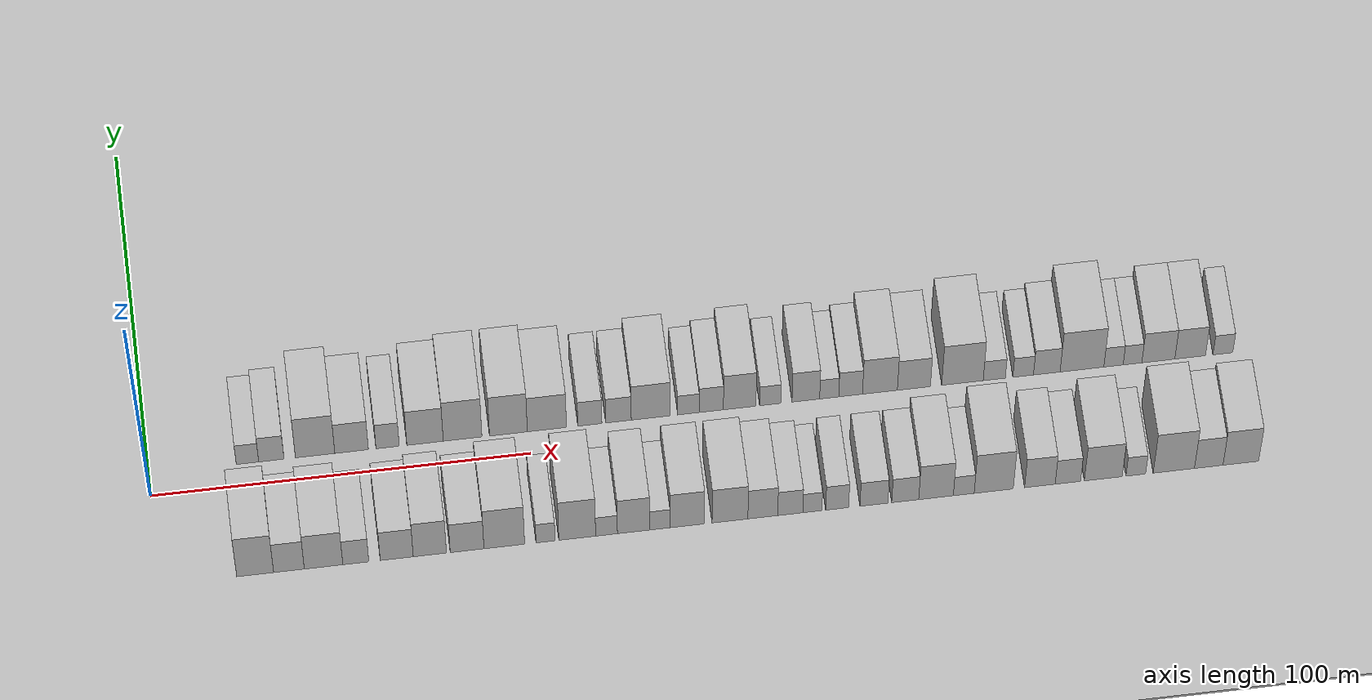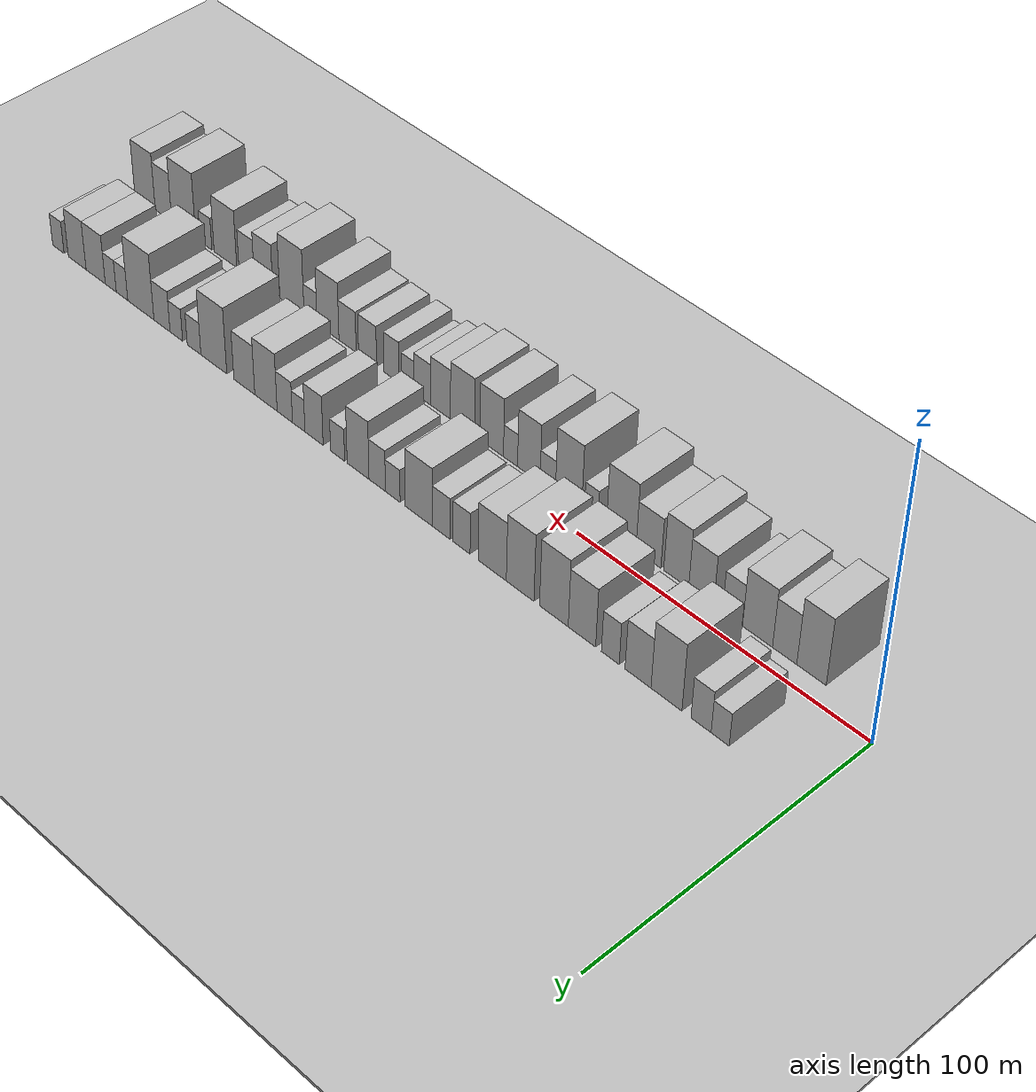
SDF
<?xml version="1.0" encoding="utf-8"?>

<sdf version="1.6">

   <world name="default">

      <gui fullscreen="0">

         <camera name="user_camera">

            <pose>-15 0 4.57585 0 0 0</pose>

            <view_controller>orbit</view_controller>

         </camera>

      </gui>

      <scene>

         <sky>

           <clouds>

             <speed>12</speed>

           </clouds>

         </sky>

         <ambient>0.4 0.4 0.4 1</ambient>

         <background>0.7 0.7 0.7 1</background>

         <shadows>1</shadows>

      </scene>

      <gravity>0 0 -9.8066</gravity>

      <magnetic_field>6e-06 2.3e-05 -4.2e-05</magnetic_field>

      <physics default="0" name="default_physics" type="ode">

         <ode>

            <solver>

               <type>quick</type>

               <iters>10</iters>

               <sor>1.0</sor>

               <use_dynamic_moi_rescaling>0</use_dynamic_moi_rescaling>

            </solver>

            <constraints>

               <cfm>0</cfm>

               <erp>0.2</erp>

               <contact_max_correcting_vel>100</contact_max_correcting_vel>

               <contact_surface_layer>0.001</contact_surface_layer>

            </constraints>

         </ode>

         <max_step_size>0.004</max_step_size>

         <real_time_factor>1</real_time_factor>

         <real_time_update_rate>250</real_time_update_rate>

      </physics>

      <light name="sun" type="directional">

         <cast_shadows>1</cast_shadows>

         <pose>0 0 10 0 0 0</pose>

         <diffuse>0.8 0.8 0.8 1</diffuse>

         <specular>0.2 0.2 0.2 1</specular>

         <attenuation>

            <range>1000</range>

            <constant>0.9</constant>

            <linear>0.01</linear>

            <quadratic>0.001</quadratic>

         </attenuation>

         <direction>-0.5 0.1 -0.9</direction>

      </light>

      <include>

         <name>ground_plane_1</name>

         <uri>model://HANNAS_ground_plane</uri>

         <pose>0 0 0  0 0 0</pose>

      </include>

      <include>

         <name>ground_plane_2</name>

         <uri>model://HANNAS_ground_plane</uri>

         <pose>100 0 0  0 0 0</pose>

      </include>

      <model name="building_1">

         <static>1</static>

         <pose frame="">25.9544 16.0000 0 0.000000 0.000000 1.570796</pose>

         <link name="link">

            <pose frame="">0 0 6.00 0 0 0</pose>

            <collision name="collision">

               <geometry>

                  <box>

                     <size>20.0000 5.9088 12.0000</size>

                  </box>

               </geometry>

               <max_contacts>10</max_contacts>

               <surface>

                  <contact>

                     <ode/>

                  </contact>

                  <bounce/>

                  <friction>

                     <torsional>

                        <ode/>

                     </torsional>

                     <ode/>

                  </friction>

               </surface>

            </collision>

            <visual name="visual">

               <cast_shadows>0</cast_shadows>

               <geometry>

                  <box>

                     <size>20.0000 5.9088 12.0000</size>

                  </box>

               </geometry>

               <material>

                  <script>

                     <uri>model://HANNAS_wall/materials/scripts</uri>

                     <uri>model://HANNAS_wall/materials/textures</uri>

                     <name>vrc/HANNAS_wall</name>

                  </script>

               </material>

            </visual>

            <self_collide>0</self_collide>

            <enable_wind>0</enable_wind>

            <kinematic>0</kinematic>

         </link>

      </model>

      <model name="building_2">

         <static>1</static>

         <pose frame="">32.2488 16.0000 0 0.000000 0.000000 1.570796</pose>

         <link name="link">

            <pose frame="">0 0 7.50 0 0 0</pose>

            <collision name="collision">

               <geometry>

                  <box>

                     <size>20.0000 6.6799 15.0000</size>

                  </box>

               </geometry>

               <max_contacts>10</max_contacts>

               <surface>

                  <contact>

                     <ode/>

                  </contact>

                  <bounce/>

                  <friction>

                     <torsional>

                        <ode/>

                     </torsional>

                     <ode/>

                  </friction>

               </surface>

            </collision>

            <visual name="visual">

               <cast_shadows>0</cast_shadows>

               <geometry>

                  <box>

                     <size>20.0000 6.6799 15.0000</size>

                  </box>

               </geometry>

               <material>

                  <script>

                     <uri>model://HANNAS_wall/materials/scripts</uri>

                     <uri>model://HANNAS_wall/materials/textures</uri>

                     <name>vrc/HANNAS_wall</name>

                  </script>

               </material>

            </visual>

            <self_collide>0</self_collide>

            <enable_wind>0</enable_wind>

            <kinematic>0</kinematic>

         </link>

      </model>

      <model name="building_3">

         <static>1</static>

         <pose frame="">43.7842 16.0000 0 0.000000 0.000000 1.570796</pose>

         <link name="link">

            <pose frame="">0 0 12.00 0 0 0</pose>

            <collision name="collision">

               <geometry>

                  <box>

                     <size>20.0000 10.3908 24.0000</size>

                  </box>

               </geometry>

               <max_contacts>10</max_contacts>

               <surface>

                  <contact>

                     <ode/>

                  </contact>

                  <bounce/>

                  <friction>

                     <torsional>

                        <ode/>

                     </torsional>

                     <ode/>

                  </friction>

               </surface>

            </collision>

            <visual name="visual">

               <cast_shadows>0</cast_shadows>

               <geometry>

                  <box>

                     <size>20.0000 10.3908 24.0000</size>

                  </box>

               </geometry>

               <material>

                  <script>

                     <uri>model://HANNAS_wall/materials/scripts</uri>

                     <uri>model://HANNAS_wall/materials/textures</uri>

                     <name>vrc/HANNAS_wall</name>

                  </script>

               </material>

            </visual>

            <self_collide>0</self_collide>

            <enable_wind>0</enable_wind>

            <kinematic>0</kinematic>

         </link>

      </model>

      <model name="building_4">

         <static>1</static>

         <pose frame="">53.4120 16.0000 0 0.000000 0.000000 1.570796</pose>

         <link name="link">

            <pose frame="">0 0 9.00 0 0 0</pose>

            <collision name="collision">

               <geometry>

                  <box>

                     <size>20.0000 8.8648 18.0000</size>

                  </box>

               </geometry>

               <max_contacts>10</max_contacts>

               <surface>

                  <contact>

                     <ode/>

                  </contact>

                  <bounce/>

                  <friction>

                     <torsional>

                        <ode/>

                     </torsional>

                     <ode/>

                  </friction>

               </surface>

            </collision>

            <visual name="visual">

               <cast_shadows>0</cast_shadows>

               <geometry>

                  <box>

                     <size>20.0000 8.8648 18.0000</size>

                  </box>

               </geometry>

               <material>

                  <script>

                     <uri>model://HANNAS_wall/materials/scripts</uri>

                     <uri>model://HANNAS_wall/materials/textures</uri>

                     <name>vrc/HANNAS_wall</name>

                  </script>

               </material>

            </visual>

            <self_collide>0</self_collide>

            <enable_wind>0</enable_wind>

            <kinematic>0</kinematic>

         </link>

      </model>

      <model name="building_5">

         <static>1</static>

         <pose frame="">62.9199 16.0000 0 0.000000 0.000000 1.570796</pose>

         <link name="link">

            <pose frame="">0 0 7.50 0 0 0</pose>

            <collision name="collision">

               <geometry>

                  <box>

                     <size>20.0000 6.1510 15.0000</size>

                  </box>

               </geometry>

               <max_contacts>10</max_contacts>

               <surface>

                  <contact>

                     <ode/>

                  </contact>

                  <bounce/>

                  <friction>

                     <torsional>

                        <ode/>

                     </torsional>

                     <ode/>

                  </friction>

               </surface>

            </collision>

            <visual name="visual">

               <cast_shadows>0</cast_shadows>

               <geometry>

                  <box>

                     <size>20.0000 6.1510 15.0000</size>

                  </box>

               </geometry>

               <material>

                  <script>

                     <uri>model://HANNAS_wall/materials/scripts</uri>

                     <uri>model://HANNAS_wall/materials/textures</uri>

                     <name>vrc/HANNAS_wall</name>

                  </script>

               </material>

            </visual>

            <self_collide>0</self_collide>

            <enable_wind>0</enable_wind>

            <kinematic>0</kinematic>

         </link>

      </model>

      <model name="building_6">

         <static>1</static>

         <pose frame="">72.8069 16.0000 0 0.000000 0.000000 1.570796</pose>

         <link name="link">

            <pose frame="">0 0 10.50 0 0 0</pose>

            <collision name="collision">

               <geometry>

                  <box>

                     <size>20.0000 9.6230 21.0000</size>

                  </box>

               </geometry>

               <max_contacts>10</max_contacts>

               <surface>

                  <contact>

                     <ode/>

                  </contact>

                  <bounce/>

                  <friction>

                     <torsional>

                        <ode/>

                     </torsional>

                     <ode/>

                  </friction>

               </surface>

            </collision>

            <visual name="visual">

               <cast_shadows>0</cast_shadows>

               <geometry>

                  <box>

                     <size>20.0000 9.6230 21.0000</size>

                  </box>

               </geometry>

               <material>

                  <script>

                     <uri>model://HANNAS_wall/materials/scripts</uri>

                     <uri>model://HANNAS_wall/materials/textures</uri>

                     <name>vrc/HANNAS_wall</name>

                  </script>

               </material>

            </visual>

            <self_collide>0</self_collide>

            <enable_wind>0</enable_wind>

            <kinematic>0</kinematic>

         </link>

      </model>

      <model name="building_7">

         <static>1</static>

         <pose frame="">82.7275 16.0000 0 0.000000 0.000000 1.570796</pose>

         <link name="link">

            <pose frame="">0 0 12.00 0 0 0</pose>

            <collision name="collision">

               <geometry>

                  <box>

                     <size>20.0000 10.2181 24.0000</size>

                  </box>

               </geometry>

               <max_contacts>10</max_contacts>

               <surface>

                  <contact>

                     <ode/>

                  </contact>

                  <bounce/>

                  <friction>

                     <torsional>

                        <ode/>

                     </torsional>

                     <ode/>

                  </friction>

               </surface>

            </collision>

            <visual name="visual">

               <cast_shadows>0</cast_shadows>

               <geometry>

                  <box>

                     <size>20.0000 10.2181 24.0000</size>

                  </box>

               </geometry>

               <material>

                  <script>

                     <uri>model://HANNAS_wall/materials/scripts</uri>

                     <uri>model://HANNAS_wall/materials/textures</uri>

                     <name>vrc/HANNAS_wall</name>

                  </script>

               </material>

            </visual>

            <self_collide>0</self_collide>

            <enable_wind>0</enable_wind>

            <kinematic>0</kinematic>

         </link>

      </model>

      <model name="building_8">

         <static>1</static>

         <pose frame="">94.8426 16.0000 0 0.000000 0.000000 1.570796</pose>

         <link name="link">

            <pose frame="">0 0 12.00 0 0 0</pose>

            <collision name="collision">

               <geometry>

                  <box>

                     <size>20.0000 10.0121 24.0000</size>

                  </box>

               </geometry>

               <max_contacts>10</max_contacts>

               <surface>

                  <contact>

                     <ode/>

                  </contact>

                  <bounce/>

                  <friction>

                     <torsional>

                        <ode/>

                     </torsional>

                     <ode/>

                  </friction>

               </surface>

            </collision>

            <visual name="visual">

               <cast_shadows>0</cast_shadows>

               <geometry>

                  <box>

                     <size>20.0000 10.0121 24.0000</size>

                  </box>

               </geometry>

               <material>

                  <script>

                     <uri>model://HANNAS_wall/materials/scripts</uri>

                     <uri>model://HANNAS_wall/materials/textures</uri>

                     <name>vrc/HANNAS_wall</name>

                  </script>

               </material>

            </visual>

            <self_collide>0</self_collide>

            <enable_wind>0</enable_wind>

            <kinematic>0</kinematic>

         </link>

      </model>

      <model name="building_9">

         <static>1</static>

         <pose frame="">105.0213 16.0000 0 0.000000 0.000000 1.570796</pose>

         <link name="link">

            <pose frame="">0 0 10.50 0 0 0</pose>

            <collision name="collision">

               <geometry>

                  <box>

                     <size>20.0000 10.3453 21.0000</size>

                  </box>

               </geometry>

               <max_contacts>10</max_contacts>

               <surface>

                  <contact>

                     <ode/>

                  </contact>

                  <bounce/>

                  <friction>

                     <torsional>

                        <ode/>

                     </torsional>

                     <ode/>

                  </friction>

               </surface>

            </collision>

            <visual name="visual">

               <cast_shadows>0</cast_shadows>

               <geometry>

                  <box>

                     <size>20.0000 10.3453 21.0000</size>

                  </box>

               </geometry>

               <material>

                  <script>

                     <uri>model://HANNAS_wall/materials/scripts</uri>

                     <uri>model://HANNAS_wall/materials/textures</uri>

                     <name>vrc/HANNAS_wall</name>

                  </script>

               </material>

            </visual>

            <self_collide>0</self_collide>

            <enable_wind>0</enable_wind>

            <kinematic>0</kinematic>

         </link>

      </model>

      <model name="building_10">

         <static>1</static>

         <pose frame="">116.3848 16.0000 0 0.000000 0.000000 1.570796</pose>

         <link name="link">

            <pose frame="">0 0 7.50 0 0 0</pose>

            <collision name="collision">

               <geometry>

                  <box>

                     <size>20.0000 6.3818 15.0000</size>

                  </box>

               </geometry>

               <max_contacts>10</max_contacts>

               <surface>

                  <contact>

                     <ode/>

                  </contact>

                  <bounce/>

                  <friction>

                     <torsional>

                        <ode/>

                     </torsional>

                     <ode/>

                  </friction>

               </surface>

            </collision>

            <visual name="visual">

               <cast_shadows>0</cast_shadows>

               <geometry>

                  <box>

                     <size>20.0000 6.3818 15.0000</size>

                  </box>

               </geometry>

               <material>

                  <script>

                     <uri>model://HANNAS_wall/materials/scripts</uri>

                     <uri>model://HANNAS_wall/materials/textures</uri>

                     <name>vrc/HANNAS_wall</name>

                  </script>

               </material>

            </visual>

            <self_collide>0</self_collide>

            <enable_wind>0</enable_wind>

            <kinematic>0</kinematic>

         </link>

      </model>

      <model name="building_11">

         <static>1</static>

         <pose frame="">123.9703 16.0000 0 0.000000 0.000000 1.570796</pose>

         <link name="link">

            <pose frame="">0 0 7.50 0 0 0</pose>

            <collision name="collision">

               <geometry>

                  <box>

                     <size>20.0000 6.7891 15.0000</size>

                  </box>

               </geometry>

               <max_contacts>10</max_contacts>

               <surface>

                  <contact>

                     <ode/>

                  </contact>

                  <bounce/>

                  <friction>

                     <torsional>

                        <ode/>

                     </torsional>

                     <ode/>

                  </friction>

               </surface>

            </collision>

            <visual name="visual">

               <cast_shadows>0</cast_shadows>

               <geometry>

                  <box>

                     <size>20.0000 6.7891 15.0000</size>

                  </box>

               </geometry>

               <material>

                  <script>

                     <uri>model://HANNAS_wall/materials/scripts</uri>

                     <uri>model://HANNAS_wall/materials/textures</uri>

                     <name>vrc/HANNAS_wall</name>

                  </script>

               </material>

            </visual>

            <self_collide>0</self_collide>

            <enable_wind>0</enable_wind>

            <kinematic>0</kinematic>

         </link>

      </model>

      <model name="building_12">

         <static>1</static>

         <pose frame="">132.5259 16.0000 0 0.000000 0.000000 1.570796</pose>

         <link name="link">

            <pose frame="">0 0 10.50 0 0 0</pose>

            <collision name="collision">

               <geometry>

                  <box>

                     <size>20.0000 10.3223 21.0000</size>

                  </box>

               </geometry>

               <max_contacts>10</max_contacts>

               <surface>

                  <contact>

                     <ode/>

                  </contact>

                  <bounce/>

                  <friction>

                     <torsional>

                        <ode/>

                     </torsional>

                     <ode/>

                  </friction>

               </surface>

            </collision>

            <visual name="visual">

               <cast_shadows>0</cast_shadows>

               <geometry>

                  <box>

                     <size>20.0000 10.3223 21.0000</size>

                  </box>

               </geometry>

               <material>

                  <script>

                     <uri>model://HANNAS_wall/materials/scripts</uri>

                     <uri>model://HANNAS_wall/materials/textures</uri>

                     <name>vrc/HANNAS_wall</name>

                  </script>

               </material>

            </visual>

            <self_collide>0</self_collide>

            <enable_wind>0</enable_wind>

            <kinematic>0</kinematic>

         </link>

      </model>

      <model name="building_13">

         <static>1</static>

         <pose frame="">142.5351 16.0000 0 0.000000 0.000000 1.570796</pose>

         <link name="link">

            <pose frame="">0 0 6.00 0 0 0</pose>

            <collision name="collision">

               <geometry>

                  <box>

                     <size>20.0000 5.6959 12.0000</size>

                  </box>

               </geometry>

               <max_contacts>10</max_contacts>

               <surface>

                  <contact>

                     <ode/>

                  </contact>

                  <bounce/>

                  <friction>

                     <torsional>

                        <ode/>

                     </torsional>

                     <ode/>

                  </friction>

               </surface>

            </collision>

            <visual name="visual">

               <cast_shadows>0</cast_shadows>

               <geometry>

                  <box>

                     <size>20.0000 5.6959 12.0000</size>

                  </box>

               </geometry>

               <material>

                  <script>

                     <uri>model://HANNAS_wall/materials/scripts</uri>

                     <uri>model://HANNAS_wall/materials/textures</uri>

                     <name>vrc/HANNAS_wall</name>

                  </script>

               </material>

            </visual>

            <self_collide>0</self_collide>

            <enable_wind>0</enable_wind>

            <kinematic>0</kinematic>

         </link>

      </model>

      <model name="building_14">

         <static>1</static>

         <pose frame="">148.5856 16.0000 0 0.000000 0.000000 1.570796</pose>

         <link name="link">

            <pose frame="">0 0 7.50 0 0 0</pose>

            <collision name="collision">

               <geometry>

                  <box>

                     <size>20.0000 6.4052 15.0000</size>

                  </box>

               </geometry>

               <max_contacts>10</max_contacts>

               <surface>

                  <contact>

                     <ode/>

                  </contact>

                  <bounce/>

                  <friction>

                     <torsional>

                        <ode/>

                     </torsional>

                     <ode/>

                  </friction>

               </surface>

            </collision>

            <visual name="visual">

               <cast_shadows>0</cast_shadows>

               <geometry>

                  <box>

                     <size>20.0000 6.4052 15.0000</size>

                  </box>

               </geometry>

               <material>

                  <script>

                     <uri>model://HANNAS_wall/materials/scripts</uri>

                     <uri>model://HANNAS_wall/materials/textures</uri>

                     <name>vrc/HANNAS_wall</name>

                  </script>

               </material>

            </visual>

            <self_collide>0</self_collide>

            <enable_wind>0</enable_wind>

            <kinematic>0</kinematic>

         </link>

      </model>

      <model name="building_15">

         <static>1</static>

         <pose frame="">156.0996 16.0000 0 0.000000 0.000000 1.570796</pose>

         <link name="link">

            <pose frame="">0 0 10.50 0 0 0</pose>

            <collision name="collision">

               <geometry>

                  <box>

                     <size>20.0000 8.6228 21.0000</size>

                  </box>

               </geometry>

               <max_contacts>10</max_contacts>

               <surface>

                  <contact>

                     <ode/>

                  </contact>

                  <bounce/>

                  <friction>

                     <torsional>

                        <ode/>

                     </torsional>

                     <ode/>

                  </friction>

               </surface>

            </collision>

            <visual name="visual">

               <cast_shadows>0</cast_shadows>

               <geometry>

                  <box>

                     <size>20.0000 8.6228 21.0000</size>

                  </box>

               </geometry>

               <material>

                  <script>

                     <uri>model://HANNAS_wall/materials/scripts</uri>

                     <uri>model://HANNAS_wall/materials/textures</uri>

                     <name>vrc/HANNAS_wall</name>

                  </script>

               </material>

            </visual>

            <self_collide>0</self_collide>

            <enable_wind>0</enable_wind>

            <kinematic>0</kinematic>

         </link>

      </model>

      <model name="building_16">

         <static>1</static>

         <pose frame="">164.2085 16.0000 0 0.000000 0.000000 1.570796</pose>

         <link name="link">

            <pose frame="">0 0 6.00 0 0 0</pose>

            <collision name="collision">

               <geometry>

                  <box>

                     <size>20.0000 5.5949 12.0000</size>

                  </box>

               </geometry>

               <max_contacts>10</max_contacts>

               <surface>

                  <contact>

                     <ode/>

                  </contact>

                  <bounce/>

                  <friction>

                     <torsional>

                        <ode/>

                     </torsional>

                     <ode/>

                  </friction>

               </surface>

            </collision>

            <visual name="visual">

               <cast_shadows>0</cast_shadows>

               <geometry>

                  <box>

                     <size>20.0000 5.5949 12.0000</size>

                  </box>

               </geometry>

               <material>

                  <script>

                     <uri>model://HANNAS_wall/materials/scripts</uri>

                     <uri>model://HANNAS_wall/materials/textures</uri>

                     <name>vrc/HANNAS_wall</name>

                  </script>

               </material>

            </visual>

            <self_collide>0</self_collide>

            <enable_wind>0</enable_wind>

            <kinematic>0</kinematic>

         </link>

      </model>

      <model name="building_17">

         <static>1</static>

         <pose frame="">173.6710 16.0000 0 0.000000 0.000000 1.570796</pose>

         <link name="link">

            <pose frame="">0 0 9.00 0 0 0</pose>

            <collision name="collision">

               <geometry>

                  <box>

                     <size>20.0000 7.3300 18.0000</size>

                  </box>

               </geometry>

               <max_contacts>10</max_contacts>

               <surface>

                  <contact>

                     <ode/>

                  </contact>

                  <bounce/>

                  <friction>

                     <torsional>

                        <ode/>

                     </torsional>

                     <ode/>

                  </friction>

               </surface>

            </collision>

            <visual name="visual">

               <cast_shadows>0</cast_shadows>

               <geometry>

                  <box>

                     <size>20.0000 7.3300 18.0000</size>

                  </box>

               </geometry>

               <material>

                  <script>

                     <uri>model://HANNAS_wall/materials/scripts</uri>

                     <uri>model://HANNAS_wall/materials/textures</uri>

                     <name>vrc/HANNAS_wall</name>

                  </script>

               </material>

            </visual>

            <self_collide>0</self_collide>

            <enable_wind>0</enable_wind>

            <kinematic>0</kinematic>

         </link>

      </model>

      <model name="building_18">

         <static>1</static>

         <pose frame="">179.8715 16.0000 0 0.000000 0.000000 1.570796</pose>

         <link name="link">

            <pose frame="">0 0 6.00 0 0 0</pose>

            <collision name="collision">

               <geometry>

                  <box>

                     <size>20.0000 5.0711 12.0000</size>

                  </box>

               </geometry>

               <max_contacts>10</max_contacts>

               <surface>

                  <contact>

                     <ode/>

                  </contact>

                  <bounce/>

                  <friction>

                     <torsional>

                        <ode/>

                     </torsional>

                     <ode/>

                  </friction>

               </surface>

            </collision>

            <visual name="visual">

               <cast_shadows>0</cast_shadows>

               <geometry>

                  <box>

                     <size>20.0000 5.0711 12.0000</size>

                  </box>

               </geometry>

               <material>

                  <script>

                     <uri>model://HANNAS_wall/materials/scripts</uri>

                     <uri>model://HANNAS_wall/materials/textures</uri>

                     <name>vrc/HANNAS_wall</name>

                  </script>

               </material>

            </visual>

            <self_collide>0</self_collide>

            <enable_wind>0</enable_wind>

            <kinematic>0</kinematic>

         </link>

      </model>

      <model name="building_19">

         <static>1</static>

         <pose frame="">185.5619 16.0000 0 0.000000 0.000000 1.570796</pose>

         <link name="link">

            <pose frame="">0 0 7.50 0 0 0</pose>

            <collision name="collision">

               <geometry>

                  <box>

                     <size>20.0000 6.3096 15.0000</size>

                  </box>

               </geometry>

               <max_contacts>10</max_contacts>

               <surface>

                  <contact>

                     <ode/>

                  </contact>

                  <bounce/>

                  <friction>

                     <torsional>

                        <ode/>

                     </torsional>

                     <ode/>

                  </friction>

               </surface>

            </collision>

            <visual name="visual">

               <cast_shadows>0</cast_shadows>

               <geometry>

                  <box>

                     <size>20.0000 6.3096 15.0000</size>

                  </box>

               </geometry>

               <material>

                  <script>

                     <uri>model://HANNAS_wall/materials/scripts</uri>

                     <uri>model://HANNAS_wall/materials/textures</uri>

                     <name>vrc/HANNAS_wall</name>

                  </script>

               </material>

            </visual>

            <self_collide>0</self_collide>

            <enable_wind>0</enable_wind>

            <kinematic>0</kinematic>

         </link>

      </model>

      <model name="building_20">

         <static>1</static>

         <pose frame="">193.3620 16.0000 0 0.000000 0.000000 1.570796</pose>

         <link name="link">

            <pose frame="">0 0 10.50 0 0 0</pose>

            <collision name="collision">

               <geometry>

                  <box>

                     <size>20.0000 9.2907 21.0000</size>

                  </box>

               </geometry>

               <max_contacts>10</max_contacts>

               <surface>

                  <contact>

                     <ode/>

                  </contact>

                  <bounce/>

                  <friction>

                     <torsional>

                        <ode/>

                     </torsional>

                     <ode/>

                  </friction>

               </surface>

            </collision>

            <visual name="visual">

               <cast_shadows>0</cast_shadows>

               <geometry>

                  <box>

                     <size>20.0000 9.2907 21.0000</size>

                  </box>

               </geometry>

               <material>

                  <script>

                     <uri>model://HANNAS_wall/materials/scripts</uri>

                     <uri>model://HANNAS_wall/materials/textures</uri>

                     <name>vrc/HANNAS_wall</name>

                  </script>

               </material>

            </visual>

            <self_collide>0</self_collide>

            <enable_wind>0</enable_wind>

            <kinematic>0</kinematic>

         </link>

      </model>

      <model name="building_21">

         <static>1</static>

         <pose frame="">202.4040 16.0000 0 0.000000 0.000000 1.570796</pose>

         <link name="link">

            <pose frame="">0 0 9.00 0 0 0</pose>

            <collision name="collision">

               <geometry>

                  <box>

                     <size>20.0000 8.7932 18.0000</size>

                  </box>

               </geometry>

               <max_contacts>10</max_contacts>

               <surface>

                  <contact>

                     <ode/>

                  </contact>

                  <bounce/>

                  <friction>

                     <torsional>

                        <ode/>

                     </torsional>

                     <ode/>

                  </friction>

               </surface>

            </collision>

            <visual name="visual">

               <cast_shadows>0</cast_shadows>

               <geometry>

                  <box>

                     <size>20.0000 8.7932 18.0000</size>

                  </box>

               </geometry>

               <material>

                  <script>

                     <uri>model://HANNAS_wall/materials/scripts</uri>

                     <uri>model://HANNAS_wall/materials/textures</uri>

                     <name>vrc/HANNAS_wall</name>

                  </script>

               </material>

            </visual>

            <self_collide>0</self_collide>

            <enable_wind>0</enable_wind>

            <kinematic>0</kinematic>

         </link>

      </model>

      <model name="building_22">

         <static>1</static>

         <pose frame="">215.3297 16.0000 0 0.000000 0.000000 1.570796</pose>

         <link name="link">

            <pose frame="">0 0 12.00 0 0 0</pose>

            <collision name="collision">

               <geometry>

                  <box>

                     <size>20.0000 11.0581 24.0000</size>

                  </box>

               </geometry>

               <max_contacts>10</max_contacts>

               <surface>

                  <contact>

                     <ode/>

                  </contact>

                  <bounce/>

                  <friction>

                     <torsional>

                        <ode/>

                     </torsional>

                     <ode/>

                  </friction>

               </surface>

            </collision>

            <visual name="visual">

               <cast_shadows>0</cast_shadows>

               <geometry>

                  <box>

                     <size>20.0000 11.0581 24.0000</size>

                  </box>

               </geometry>

               <material>

                  <script>

                     <uri>model://HANNAS_wall/materials/scripts</uri>

                     <uri>model://HANNAS_wall/materials/textures</uri>

                     <name>vrc/HANNAS_wall</name>

                  </script>

               </material>

            </visual>

            <self_collide>0</self_collide>

            <enable_wind>0</enable_wind>

            <kinematic>0</kinematic>

         </link>

      </model>

      <model name="building_23">

         <static>1</static>

         <pose frame="">223.8093 16.0000 0 0.000000 0.000000 1.570796</pose>

         <link name="link">

            <pose frame="">0 0 6.00 0 0 0</pose>

            <collision name="collision">

               <geometry>

                  <box>

                     <size>20.0000 5.9010 12.0000</size>

                  </box>

               </geometry>

               <max_contacts>10</max_contacts>

               <surface>

                  <contact>

                     <ode/>

                  </contact>

                  <bounce/>

                  <friction>

                     <torsional>

                        <ode/>

                     </torsional>

                     <ode/>

                  </friction>

               </surface>

            </collision>

            <visual name="visual">

               <cast_shadows>0</cast_shadows>

               <geometry>

                  <box>

                     <size>20.0000 5.9010 12.0000</size>

                  </box>

               </geometry>

               <material>

                  <script>

                     <uri>model://HANNAS_wall/materials/scripts</uri>

                     <uri>model://HANNAS_wall/materials/textures</uri>

                     <name>vrc/HANNAS_wall</name>

                  </script>

               </material>

            </visual>

            <self_collide>0</self_collide>

            <enable_wind>0</enable_wind>

            <kinematic>0</kinematic>

         </link>

      </model>

      <model name="building_24">

         <static>1</static>

         <pose frame="">231.5035 16.0000 0 0.000000 0.000000 1.570796</pose>

         <link name="link">

            <pose frame="">0 0 6.00 0 0 0</pose>

            <collision name="collision">

               <geometry>

                  <box>

                     <size>20.0000 5.4875 12.0000</size>

                  </box>

               </geometry>

               <max_contacts>10</max_contacts>

               <surface>

                  <contact>

                     <ode/>

                  </contact>

                  <bounce/>

                  <friction>

                     <torsional>

                        <ode/>

                     </torsional>

                     <ode/>

                  </friction>

               </surface>

            </collision>

            <visual name="visual">

               <cast_shadows>0</cast_shadows>

               <geometry>

                  <box>

                     <size>20.0000 5.4875 12.0000</size>

                  </box>

               </geometry>

               <material>

                  <script>

                     <uri>model://HANNAS_wall/materials/scripts</uri>

                     <uri>model://HANNAS_wall/materials/textures</uri>

                     <name>vrc/HANNAS_wall</name>

                  </script>

               </material>

            </visual>

            <self_collide>0</self_collide>

            <enable_wind>0</enable_wind>

            <kinematic>0</kinematic>

         </link>

      </model>

      <model name="building_25">

         <static>1</static>

         <pose frame="">237.7894 16.0000 0 0.000000 0.000000 1.570796</pose>

         <link name="link">

            <pose frame="">0 0 7.50 0 0 0</pose>

            <collision name="collision">

               <geometry>

                  <box>

                     <size>20.0000 7.0842 15.0000</size>

                  </box>

               </geometry>

               <max_contacts>10</max_contacts>

               <surface>

                  <contact>

                     <ode/>

                  </contact>

                  <bounce/>

                  <friction>

                     <torsional>

                        <ode/>

                     </torsional>

                     <ode/>

                  </friction>

               </surface>

            </collision>

            <visual name="visual">

               <cast_shadows>0</cast_shadows>

               <geometry>

                  <box>

                     <size>20.0000 7.0842 15.0000</size>

                  </box>

               </geometry>

               <material>

                  <script>

                     <uri>model://HANNAS_wall/materials/scripts</uri>

                     <uri>model://HANNAS_wall/materials/textures</uri>

                     <name>vrc/HANNAS_wall</name>

                  </script>

               </material>

            </visual>

            <self_collide>0</self_collide>

            <enable_wind>0</enable_wind>

            <kinematic>0</kinematic>

         </link>

      </model>

      <model name="building_26">

         <static>1</static>

         <pose frame="">247.1757 16.0000 0 0.000000 0.000000 1.570796</pose>

         <link name="link">

            <pose frame="">0 0 12.00 0 0 0</pose>

            <collision name="collision">

               <geometry>

                  <box>

                     <size>20.0000 11.6884 24.0000</size>

                  </box>

               </geometry>

               <max_contacts>10</max_contacts>

               <surface>

                  <contact>

                     <ode/>

                  </contact>

                  <bounce/>

                  <friction>

                     <torsional>

                        <ode/>

                     </torsional>

                     <ode/>

                  </friction>

               </surface>

            </collision>

            <visual name="visual">

               <cast_shadows>0</cast_shadows>

               <geometry>

                  <box>

                     <size>20.0000 11.6884 24.0000</size>

                  </box>

               </geometry>

               <material>

                  <script>

                     <uri>model://HANNAS_wall/materials/scripts</uri>

                     <uri>model://HANNAS_wall/materials/textures</uri>

                     <name>vrc/HANNAS_wall</name>

                  </script>

               </material>

            </visual>

            <self_collide>0</self_collide>

            <enable_wind>0</enable_wind>

            <kinematic>0</kinematic>

         </link>

      </model>

      <model name="building_27">

         <static>1</static>

         <pose frame="">255.6017 16.0000 0 0.000000 0.000000 1.570796</pose>

         <link name="link">

            <pose frame="">0 0 6.00 0 0 0</pose>

            <collision name="collision">

               <geometry>

                  <box>

                     <size>20.0000 5.1636 12.0000</size>

                  </box>

               </geometry>

               <max_contacts>10</max_contacts>

               <surface>

                  <contact>

                     <ode/>

                  </contact>

                  <bounce/>

                  <friction>

                     <torsional>

                        <ode/>

                     </torsional>

                     <ode/>

                  </friction>

               </surface>

            </collision>

            <visual name="visual">

               <cast_shadows>0</cast_shadows>

               <geometry>

                  <box>

                     <size>20.0000 5.1636 12.0000</size>

                  </box>

               </geometry>

               <material>

                  <script>

                     <uri>model://HANNAS_wall/materials/scripts</uri>

                     <uri>model://HANNAS_wall/materials/textures</uri>

                     <name>vrc/HANNAS_wall</name>

                  </script>

               </material>

            </visual>

            <self_collide>0</self_collide>

            <enable_wind>0</enable_wind>

            <kinematic>0</kinematic>

         </link>

      </model>

      <model name="building_28">

         <static>1</static>

         <pose frame="">260.6690 16.0000 0 0.000000 0.000000 1.570796</pose>

         <link name="link">

            <pose frame="">0 0 6.00 0 0 0</pose>

            <collision name="collision">

               <geometry>

                  <box>

                     <size>20.0000 4.9711 12.0000</size>

                  </box>

               </geometry>

               <max_contacts>10</max_contacts>

               <surface>

                  <contact>

                     <ode/>

                  </contact>

                  <bounce/>

                  <friction>

                     <torsional>

                        <ode/>

                     </torsional>

                     <ode/>

                  </friction>

               </surface>

            </collision>

            <visual name="visual">

               <cast_shadows>0</cast_shadows>

               <geometry>

                  <box>

                     <size>20.0000 4.9711 12.0000</size>

                  </box>

               </geometry>

               <material>

                  <script>

                     <uri>model://HANNAS_wall/materials/scripts</uri>

                     <uri>model://HANNAS_wall/materials/textures</uri>

                     <name>vrc/HANNAS_wall</name>

                  </script>

               </material>

            </visual>

            <self_collide>0</self_collide>

            <enable_wind>0</enable_wind>

            <kinematic>0</kinematic>

         </link>

      </model>

      <model name="building_29">

         <static>1</static>

         <pose frame="">267.5593 16.0000 0 0.000000 0.000000 1.570796</pose>

         <link name="link">

            <pose frame="">0 0 9.00 0 0 0</pose>

            <collision name="collision">

               <geometry>

                  <box>

                     <size>20.0000 8.8094 18.0000</size>

                  </box>

               </geometry>

               <max_contacts>10</max_contacts>

               <surface>

                  <contact>

                     <ode/>

                  </contact>

                  <bounce/>

                  <friction>

                     <torsional>

                        <ode/>

                     </torsional>

                     <ode/>

                  </friction>

               </surface>

            </collision>

            <visual name="visual">

               <cast_shadows>0</cast_shadows>

               <geometry>

                  <box>

                     <size>20.0000 8.8094 18.0000</size>

                  </box>

               </geometry>

               <material>

                  <script>

                     <uri>model://HANNAS_wall/materials/scripts</uri>

                     <uri>model://HANNAS_wall/materials/textures</uri>

                     <name>vrc/HANNAS_wall</name>

                  </script>

               </material>

            </visual>

            <self_collide>0</self_collide>

            <enable_wind>0</enable_wind>

            <kinematic>0</kinematic>

         </link>

      </model>

      <model name="building_30">

         <static>1</static>

         <pose frame="">276.0621 16.0000 0 0.000000 0.000000 1.570796</pose>

         <link name="link">

            <pose frame="">0 0 9.00 0 0 0</pose>

            <collision name="collision">

               <geometry>

                  <box>

                     <size>20.0000 8.1962 18.0000</size>

                  </box>

               </geometry>

               <max_contacts>10</max_contacts>

               <surface>

                  <contact>

                     <ode/>

                  </contact>

                  <bounce/>

                  <friction>

                     <torsional>

                        <ode/>

                     </torsional>

                     <ode/>

                  </friction>

               </surface>

            </collision>

            <visual name="visual">

               <cast_shadows>0</cast_shadows>

               <geometry>

                  <box>

                     <size>20.0000 8.1962 18.0000</size>

                  </box>

               </geometry>

               <material>

                  <script>

                     <uri>model://HANNAS_wall/materials/scripts</uri>

                     <uri>model://HANNAS_wall/materials/textures</uri>

                     <name>vrc/HANNAS_wall</name>

                  </script>

               </material>

            </visual>

            <self_collide>0</self_collide>

            <enable_wind>0</enable_wind>

            <kinematic>0</kinematic>

         </link>

      </model>

      <model name="building_31">

         <static>1</static>

         <pose frame="">284.8099 16.0000 0 0.000000 0.000000 1.570796</pose>

         <link name="link">

            <pose frame="">0 0 6.00 0 0 0</pose>

            <collision name="collision">

               <geometry>

                  <box>

                     <size>20.0000 5.2995 12.0000</size>

                  </box>

               </geometry>

               <max_contacts>10</max_contacts>

               <surface>

                  <contact>

                     <ode/>

                  </contact>

                  <bounce/>

                  <friction>

                     <torsional>

                        <ode/>

                     </torsional>

                     <ode/>

                  </friction>

               </surface>

            </collision>

            <visual name="visual">

               <cast_shadows>0</cast_shadows>

               <geometry>

                  <box>

                     <size>20.0000 5.2995 12.0000</size>

                  </box>

               </geometry>

               <material>

                  <script>

                     <uri>model://HANNAS_wall/materials/scripts</uri>

                     <uri>model://HANNAS_wall/materials/textures</uri>

                     <name>vrc/HANNAS_wall</name>

                  </script>

               </material>

            </visual>

            <self_collide>0</self_collide>

            <enable_wind>0</enable_wind>

            <kinematic>0</kinematic>

         </link>

      </model>

      <model name="building_32">

         <static>1</static>

         <pose frame="">24.8253 -16.0000 0 0.000000 0.000000 1.570796</pose>

         <link name="link">

            <pose frame="">0 0 12.00 0 0 0</pose>

            <collision name="collision">

               <geometry>

                  <box>

                     <size>20.0000 9.6506 24.0000</size>

                  </box>

               </geometry>

               <max_contacts>10</max_contacts>

               <surface>

                  <contact>

                     <ode/>

                  </contact>

                  <bounce/>

                  <friction>

                     <torsional>

                        <ode/>

                     </torsional>

                     <ode/>

                  </friction>

               </surface>

            </collision>

            <visual name="visual">

               <cast_shadows>0</cast_shadows>

               <geometry>

                  <box>

                     <size>20.0000 9.6506 24.0000</size>

                  </box>

               </geometry>

               <material>

                  <script>

                     <uri>model://HANNAS_wall/materials/scripts</uri>

                     <uri>model://HANNAS_wall/materials/textures</uri>

                     <name>vrc/HANNAS_wall</name>

                  </script>

               </material>

            </visual>

            <self_collide>0</self_collide>

            <enable_wind>0</enable_wind>

            <kinematic>0</kinematic>

         </link>

      </model>

      <model name="building_33">

         <static>1</static>

         <pose frame="">33.6735 -16.0000 0 0.000000 0.000000 1.570796</pose>

         <link name="link">

            <pose frame="">0 0 9.00 0 0 0</pose>

            <collision name="collision">

               <geometry>

                  <box>

                     <size>20.0000 8.0458 18.0000</size>

                  </box>

               </geometry>

               <max_contacts>10</max_contacts>

               <surface>

                  <contact>

                     <ode/>

                  </contact>

                  <bounce/>

                  <friction>

                     <torsional>

                        <ode/>

                     </torsional>

                     <ode/>

                  </friction>

               </surface>

            </collision>

            <visual name="visual">

               <cast_shadows>0</cast_shadows>

               <geometry>

                  <box>

                     <size>20.0000 8.0458 18.0000</size>

                  </box>

               </geometry>

               <material>

                  <script>

                     <uri>model://HANNAS_wall/materials/scripts</uri>

                     <uri>model://HANNAS_wall/materials/textures</uri>

                     <name>vrc/HANNAS_wall</name>

                  </script>

               </material>

            </visual>

            <self_collide>0</self_collide>

            <enable_wind>0</enable_wind>

            <kinematic>0</kinematic>

         </link>

      </model>

      <model name="building_34">

         <static>1</static>

         <pose frame="">42.7346 -16.0000 0 0.000000 0.000000 1.570796</pose>

         <link name="link">

            <pose frame="">0 0 10.50 0 0 0</pose>

            <collision name="collision">

               <geometry>

                  <box>

                     <size>20.0000 10.0762 21.0000</size>

                  </box>

               </geometry>

               <max_contacts>10</max_contacts>

               <surface>

                  <contact>

                     <ode/>

                  </contact>

                  <bounce/>

                  <friction>

                     <torsional>

                        <ode/>

                     </torsional>

                     <ode/>

                  </friction>

               </surface>

            </collision>

            <visual name="visual">

               <cast_shadows>0</cast_shadows>

               <geometry>

                  <box>

                     <size>20.0000 10.0762 21.0000</size>

                  </box>

               </geometry>

               <material>

                  <script>

                     <uri>model://HANNAS_wall/materials/scripts</uri>

                     <uri>model://HANNAS_wall/materials/textures</uri>

                     <name>vrc/HANNAS_wall</name>

                  </script>

               </material>

            </visual>

            <self_collide>0</self_collide>

            <enable_wind>0</enable_wind>

            <kinematic>0</kinematic>

         </link>

      </model>

      <model name="building_35">

         <static>1</static>

         <pose frame="">51.1768 -16.0000 0 0.000000 0.000000 1.570796</pose>

         <link name="link">

            <pose frame="">0 0 7.50 0 0 0</pose>

            <collision name="collision">

               <geometry>

                  <box>

                     <size>20.0000 6.8083 15.0000</size>

                  </box>

               </geometry>

               <max_contacts>10</max_contacts>

               <surface>

                  <contact>

                     <ode/>

                  </contact>

                  <bounce/>

                  <friction>

                     <torsional>

                        <ode/>

                     </torsional>

                     <ode/>

                  </friction>

               </surface>

            </collision>

            <visual name="visual">

               <cast_shadows>0</cast_shadows>

               <geometry>

                  <box>

                     <size>20.0000 6.8083 15.0000</size>

                  </box>

               </geometry>

               <material>

                  <script>

                     <uri>model://HANNAS_wall/materials/scripts</uri>

                     <uri>model://HANNAS_wall/materials/textures</uri>

                     <name>vrc/HANNAS_wall</name>

                  </script>

               </material>

            </visual>

            <self_collide>0</self_collide>

            <enable_wind>0</enable_wind>

            <kinematic>0</kinematic>

         </link>

      </model>

      <model name="building_36">

         <static>1</static>

         <pose frame="">61.9040 -16.0000 0 0.000000 0.000000 1.570796</pose>

         <link name="link">

            <pose frame="">0 0 9.00 0 0 0</pose>

            <collision name="collision">

               <geometry>

                  <box>

                     <size>20.0000 8.6461 18.0000</size>

                  </box>

               </geometry>

               <max_contacts>10</max_contacts>

               <surface>

                  <contact>

                     <ode/>

                  </contact>

                  <bounce/>

                  <friction>

                     <torsional>

                        <ode/>

                     </torsional>

                     <ode/>

                  </friction>

               </surface>

            </collision>

            <visual name="visual">

               <cast_shadows>0</cast_shadows>

               <geometry>

                  <box>

                     <size>20.0000 8.6461 18.0000</size>

                  </box>

               </geometry>

               <material>

                  <script>

                     <uri>model://HANNAS_wall/materials/scripts</uri>

                     <uri>model://HANNAS_wall/materials/textures</uri>

                     <name>vrc/HANNAS_wall</name>

                  </script>

               </material>

            </visual>

            <self_collide>0</self_collide>

            <enable_wind>0</enable_wind>

            <kinematic>0</kinematic>

         </link>

      </model>

      <model name="building_37">

         <static>1</static>

         <pose frame="">70.5800 -16.0000 0 0.000000 0.000000 1.570796</pose>

         <link name="link">

            <pose frame="">0 0 10.50 0 0 0</pose>

            <collision name="collision">

               <geometry>

                  <box>

                     <size>20.0000 8.7058 21.0000</size>

                  </box>

               </geometry>

               <max_contacts>10</max_contacts>

               <surface>

                  <contact>

                     <ode/>

                  </contact>

                  <bounce/>

                  <friction>

                     <torsional>

                        <ode/>

                     </torsional>

                     <ode/>

                  </friction>

               </surface>

            </collision>

            <visual name="visual">

               <cast_shadows>0</cast_shadows>

               <geometry>

                  <box>

                     <size>20.0000 8.7058 21.0000</size>

                  </box>

               </geometry>

               <material>

                  <script>

                     <uri>model://HANNAS_wall/materials/scripts</uri>

                     <uri>model://HANNAS_wall/materials/textures</uri>

                     <name>vrc/HANNAS_wall</name>

                  </script>

               </material>

            </visual>

            <self_collide>0</self_collide>

            <enable_wind>0</enable_wind>

            <kinematic>0</kinematic>

         </link>

      </model>

      <model name="building_38">

         <static>1</static>

         <pose frame="">80.3602 -16.0000 0 0.000000 0.000000 1.570796</pose>

         <link name="link">

            <pose frame="">0 0 9.00 0 0 0</pose>

            <collision name="collision">

               <geometry>

                  <box>

                     <size>20.0000 8.8546 18.0000</size>

                  </box>

               </geometry>

               <max_contacts>10</max_contacts>

               <surface>

                  <contact>

                     <ode/>

                  </contact>

                  <bounce/>

                  <friction>

                     <torsional>

                        <ode/>

                     </torsional>

                     <ode/>

                  </friction>

               </surface>

            </collision>

            <visual name="visual">

               <cast_shadows>0</cast_shadows>

               <geometry>

                  <box>

                     <size>20.0000 8.8546 18.0000</size>

                  </box>

               </geometry>

               <material>

                  <script>

                     <uri>model://HANNAS_wall/materials/scripts</uri>

                     <uri>model://HANNAS_wall/materials/textures</uri>

                     <name>vrc/HANNAS_wall</name>

                  </script>

               </material>

            </visual>

            <self_collide>0</self_collide>

            <enable_wind>0</enable_wind>

            <kinematic>0</kinematic>

         </link>

      </model>

      <model name="building_39">

         <static>1</static>

         <pose frame="">90.1226 -16.0000 0 0.000000 0.000000 1.570796</pose>

         <link name="link">

            <pose frame="">0 0 12.00 0 0 0</pose>

            <collision name="collision">

               <geometry>

                  <box>

                     <size>20.0000 10.6703 24.0000</size>

                  </box>

               </geometry>

               <max_contacts>10</max_contacts>

               <surface>

                  <contact>

                     <ode/>

                  </contact>

                  <bounce/>

                  <friction>

                     <torsional>

                        <ode/>

                     </torsional>

                     <ode/>

                  </friction>

               </surface>

            </collision>

            <visual name="visual">

               <cast_shadows>0</cast_shadows>

               <geometry>

                  <box>

                     <size>20.0000 10.6703 24.0000</size>

                  </box>

               </geometry>

               <material>

                  <script>

                     <uri>model://HANNAS_wall/materials/scripts</uri>

                     <uri>model://HANNAS_wall/materials/textures</uri>

                     <name>vrc/HANNAS_wall</name>

                  </script>

               </material>

            </visual>

            <self_collide>0</self_collide>

            <enable_wind>0</enable_wind>

            <kinematic>0</kinematic>

         </link>

      </model>

      <model name="building_40">

         <static>1</static>

         <pose frame="">100.9520 -16.0000 0 0.000000 0.000000 1.570796</pose>

         <link name="link">

            <pose frame="">0 0 6.00 0 0 0</pose>

            <collision name="collision">

               <geometry>

                  <box>

                     <size>20.0000 4.9884 12.0000</size>

                  </box>

               </geometry>

               <max_contacts>10</max_contacts>

               <surface>

                  <contact>

                     <ode/>

                  </contact>

                  <bounce/>

                  <friction>

                     <torsional>

                        <ode/>

                     </torsional>

                     <ode/>

                  </friction>

               </surface>

            </collision>

            <visual name="visual">

               <cast_shadows>0</cast_shadows>

               <geometry>

                  <box>

                     <size>20.0000 4.9884 12.0000</size>

                  </box>

               </geometry>

               <material>

                  <script>

                     <uri>model://HANNAS_wall/materials/scripts</uri>

                     <uri>model://HANNAS_wall/materials/textures</uri>

                     <name>vrc/HANNAS_wall</name>

                  </script>

               </material>

            </visual>

            <self_collide>0</self_collide>

            <enable_wind>0</enable_wind>

            <kinematic>0</kinematic>

         </link>

      </model>

      <model name="building_41">

         <static>1</static>

         <pose frame="">109.2826 -16.0000 0 0.000000 0.000000 1.570796</pose>

         <link name="link">

            <pose frame="">0 0 12.00 0 0 0</pose>

            <collision name="collision">

               <geometry>

                  <box>

                     <size>20.0000 9.6730 24.0000</size>

                  </box>

               </geometry>

               <max_contacts>10</max_contacts>

               <surface>

                  <contact>

                     <ode/>

                  </contact>

                  <bounce/>

                  <friction>

                     <torsional>

                        <ode/>

                     </torsional>

                     <ode/>

                  </friction>

               </surface>

            </collision>

            <visual name="visual">

               <cast_shadows>0</cast_shadows>

               <geometry>

                  <box>

                     <size>20.0000 9.6730 24.0000</size>

                  </box>

               </geometry>

               <material>

                  <script>

                     <uri>model://HANNAS_wall/materials/scripts</uri>

                     <uri>model://HANNAS_wall/materials/textures</uri>

                     <name>vrc/HANNAS_wall</name>

                  </script>

               </material>

            </visual>

            <self_collide>0</self_collide>

            <enable_wind>0</enable_wind>

            <kinematic>0</kinematic>

         </link>

      </model>

      <model name="building_42">

         <static>1</static>

         <pose frame="">116.9837 -16.0000 0 0.000000 0.000000 1.570796</pose>

         <link name="link">

            <pose frame="">0 0 6.00 0 0 0</pose>

            <collision name="collision">

               <geometry>

                  <box>

                     <size>20.0000 5.7291 12.0000</size>

                  </box>

               </geometry>

               <max_contacts>10</max_contacts>

               <surface>

                  <contact>

                     <ode/>

                  </contact>

                  <bounce/>

                  <friction>

                     <torsional>

                        <ode/>

                     </torsional>

                     <ode/>

                  </friction>

               </surface>

            </collision>

            <visual name="visual">

               <cast_shadows>0</cast_shadows>

               <geometry>

                  <box>

                     <size>20.0000 5.7291 12.0000</size>

                  </box>

               </geometry>

               <material>

                  <script>

                     <uri>model://HANNAS_wall/materials/scripts</uri>

                     <uri>model://HANNAS_wall/materials/textures</uri>

                     <name>vrc/HANNAS_wall</name>

                  </script>

               </material>

            </visual>

            <self_collide>0</self_collide>

            <enable_wind>0</enable_wind>

            <kinematic>0</kinematic>

         </link>

      </model>

      <model name="building_43">

         <static>1</static>

         <pose frame="">124.0921 -16.0000 0 0.000000 0.000000 1.570796</pose>

         <link name="link">

            <pose frame="">0 0 10.50 0 0 0</pose>

            <collision name="collision">

               <geometry>

                  <box>

                     <size>20.0000 8.4878 21.0000</size>

                  </box>

               </geometry>

               <max_contacts>10</max_contacts>

               <surface>

                  <contact>

                     <ode/>

                  </contact>

                  <bounce/>

                  <friction>

                     <torsional>

                        <ode/>

                     </torsional>

                     <ode/>

                  </friction>

               </surface>

            </collision>

            <visual name="visual">

               <cast_shadows>0</cast_shadows>

               <geometry>

                  <box>

                     <size>20.0000 8.4878 21.0000</size>

                  </box>

               </geometry>

               <material>

                  <script>

                     <uri>model://HANNAS_wall/materials/scripts</uri>

                     <uri>model://HANNAS_wall/materials/textures</uri>

                     <name>vrc/HANNAS_wall</name>

                  </script>

               </material>

            </visual>

            <self_collide>0</self_collide>

            <enable_wind>0</enable_wind>

            <kinematic>0</kinematic>

         </link>

      </model>

      <model name="building_44">

         <static>1</static>

         <pose frame="">131.0113 -16.0000 0 0.000000 0.000000 1.570796</pose>

         <link name="link">

            <pose frame="">0 0 6.00 0 0 0</pose>

            <collision name="collision">

               <geometry>

                  <box>

                     <size>20.0000 5.3506 12.0000</size>

                  </box>

               </geometry>

               <max_contacts>10</max_contacts>

               <surface>

                  <contact>

                     <ode/>

                  </contact>

                  <bounce/>

                  <friction>

                     <torsional>

                        <ode/>

                     </torsional>

                     <ode/>

                  </friction>

               </surface>

            </collision>

            <visual name="visual">

               <cast_shadows>0</cast_shadows>

               <geometry>

                  <box>

                     <size>20.0000 5.3506 12.0000</size>

                  </box>

               </geometry>

               <material>

                  <script>

                     <uri>model://HANNAS_wall/materials/scripts</uri>

                     <uri>model://HANNAS_wall/materials/textures</uri>

                     <name>vrc/HANNAS_wall</name>

                  </script>

               </material>

            </visual>

            <self_collide>0</self_collide>

            <enable_wind>0</enable_wind>

            <kinematic>0</kinematic>

         </link>

      </model>

      <model name="building_45">

         <static>1</static>

         <pose frame="">138.2235 -16.0000 0 0.000000 0.000000 1.570796</pose>

         <link name="link">

            <pose frame="">0 0 10.50 0 0 0</pose>

            <collision name="collision">

               <geometry>

                  <box>

                     <size>20.0000 9.0737 21.0000</size>

                  </box>

               </geometry>

               <max_contacts>10</max_contacts>

               <surface>

                  <contact>

                     <ode/>

                  </contact>

                  <bounce/>

                  <friction>

                     <torsional>

                        <ode/>

                     </torsional>

                     <ode/>

                  </friction>

               </surface>

            </collision>

            <visual name="visual">

               <cast_shadows>0</cast_shadows>

               <geometry>

                  <box>

                     <size>20.0000 9.0737 21.0000</size>

                  </box>

               </geometry>

               <material>

                  <script>

                     <uri>model://HANNAS_wall/materials/scripts</uri>

                     <uri>model://HANNAS_wall/materials/textures</uri>

                     <name>vrc/HANNAS_wall</name>

                  </script>

               </material>

            </visual>

            <self_collide>0</self_collide>

            <enable_wind>0</enable_wind>

            <kinematic>0</kinematic>

         </link>

      </model>

      <model name="building_46">

         <static>1</static>

         <pose frame="">149.4765 -16.0000 0 0.000000 0.000000 1.570796</pose>

         <link name="link">

            <pose frame="">0 0 10.50 0 0 0</pose>

            <collision name="collision">

               <geometry>

                  <box>

                     <size>20.0000 9.4323 21.0000</size>

                  </box>

               </geometry>

               <max_contacts>10</max_contacts>

               <surface>

                  <contact>

                     <ode/>

                  </contact>

                  <bounce/>

                  <friction>

                     <torsional>

                        <ode/>

                     </torsional>

                     <ode/>

                  </friction>

               </surface>

            </collision>

            <visual name="visual">

               <cast_shadows>0</cast_shadows>

               <geometry>

                  <box>

                     <size>20.0000 9.4323 21.0000</size>

                  </box>

               </geometry>

               <material>

                  <script>

                     <uri>model://HANNAS_wall/materials/scripts</uri>

                     <uri>model://HANNAS_wall/materials/textures</uri>

                     <name>vrc/HANNAS_wall</name>

                  </script>

               </material>

            </visual>

            <self_collide>0</self_collide>

            <enable_wind>0</enable_wind>

            <kinematic>0</kinematic>

         </link>

      </model>

      <model name="building_47">

         <static>1</static>

         <pose frame="">158.1193 -16.0000 0 0.000000 0.000000 1.570796</pose>

         <link name="link">

            <pose frame="">0 0 9.00 0 0 0</pose>

            <collision name="collision">

               <geometry>

                  <box>

                     <size>20.0000 7.8533 18.0000</size>

                  </box>

               </geometry>

               <max_contacts>10</max_contacts>

               <surface>

                  <contact>

                     <ode/>

                  </contact>

                  <bounce/>

                  <friction>

                     <torsional>

                        <ode/>

                     </torsional>

                     <ode/>

                  </friction>

               </surface>

            </collision>

            <visual name="visual">

               <cast_shadows>0</cast_shadows>

               <geometry>

                  <box>

                     <size>20.0000 7.8533 18.0000</size>

                  </box>

               </geometry>

               <material>

                  <script>

                     <uri>model://HANNAS_wall/materials/scripts</uri>

                     <uri>model://HANNAS_wall/materials/textures</uri>

                     <name>vrc/HANNAS_wall</name>

                  </script>

               </material>

            </visual>

            <self_collide>0</self_collide>

            <enable_wind>0</enable_wind>

            <kinematic>0</kinematic>

         </link>

      </model>

      <model name="building_48">

         <static>1</static>

         <pose frame="">165.3548 -16.0000 0 0.000000 0.000000 1.570796</pose>

         <link name="link">

            <pose frame="">0 0 7.50 0 0 0</pose>

            <collision name="collision">

               <geometry>

                  <box>

                     <size>20.0000 6.6178 15.0000</size>

                  </box>

               </geometry>

               <max_contacts>10</max_contacts>

               <surface>

                  <contact>

                     <ode/>

                  </contact>

                  <bounce/>

                  <friction>

                     <torsional>

                        <ode/>

                     </torsional>

                     <ode/>

                  </friction>

               </surface>

            </collision>

            <visual name="visual">

               <cast_shadows>0</cast_shadows>

               <geometry>

                  <box>

                     <size>20.0000 6.6178 15.0000</size>

                  </box>

               </geometry>

               <material>

                  <script>

                     <uri>model://HANNAS_wall/materials/scripts</uri>

                     <uri>model://HANNAS_wall/materials/textures</uri>

                     <name>vrc/HANNAS_wall</name>

                  </script>

               </material>

            </visual>

            <self_collide>0</self_collide>

            <enable_wind>0</enable_wind>

            <kinematic>0</kinematic>

         </link>

      </model>

      <model name="building_49">

         <static>1</static>

         <pose frame="">171.1780 -16.0000 0 0.000000 0.000000 1.570796</pose>

         <link name="link">

            <pose frame="">0 0 6.00 0 0 0</pose>

            <collision name="collision">

               <geometry>

                  <box>

                     <size>20.0000 5.0285 12.0000</size>

                  </box>

               </geometry>

               <max_contacts>10</max_contacts>

               <surface>

                  <contact>

                     <ode/>

                  </contact>

                  <bounce/>

                  <friction>

                     <torsional>

                        <ode/>

                     </torsional>

                     <ode/>

                  </friction>

               </surface>

            </collision>

            <visual name="visual">

               <cast_shadows>0</cast_shadows>

               <geometry>

                  <box>

                     <size>20.0000 5.0285 12.0000</size>

                  </box>

               </geometry>

               <material>

                  <script>

                     <uri>model://HANNAS_wall/materials/scripts</uri>

                     <uri>model://HANNAS_wall/materials/textures</uri>

                     <name>vrc/HANNAS_wall</name>

                  </script>

               </material>

            </visual>

            <self_collide>0</self_collide>

            <enable_wind>0</enable_wind>

            <kinematic>0</kinematic>

         </link>

      </model>

      <model name="building_50">

         <static>1</static>

         <pose frame="">177.7196 -16.0000 0 0.000000 0.000000 1.570796</pose>

         <link name="link">

            <pose frame="">0 0 7.50 0 0 0</pose>

            <collision name="collision">

               <geometry>

                  <box>

                     <size>20.0000 6.0546 15.0000</size>

                  </box>

               </geometry>

               <max_contacts>10</max_contacts>

               <surface>

                  <contact>

                     <ode/>

                  </contact>

                  <bounce/>

                  <friction>

                     <torsional>

                        <ode/>

                     </torsional>

                     <ode/>

                  </friction>

               </surface>

            </collision>

            <visual name="visual">

               <cast_shadows>0</cast_shadows>

               <geometry>

                  <box>

                     <size>20.0000 6.0546 15.0000</size>

                  </box>

               </geometry>

               <material>

                  <script>

                     <uri>model://HANNAS_wall/materials/scripts</uri>

                     <uri>model://HANNAS_wall/materials/textures</uri>

                     <name>vrc/HANNAS_wall</name>

                  </script>

               </material>

            </visual>

            <self_collide>0</self_collide>

            <enable_wind>0</enable_wind>

            <kinematic>0</kinematic>

         </link>

      </model>

      <model name="building_51">

         <static>1</static>

         <pose frame="">187.4385 -16.0000 0 0.000000 0.000000 1.570796</pose>

         <link name="link">

            <pose frame="">0 0 7.50 0 0 0</pose>

            <collision name="collision">

               <geometry>

                  <box>

                     <size>20.0000 7.3833 15.0000</size>

                  </box>

               </geometry>

               <max_contacts>10</max_contacts>

               <surface>

                  <contact>

                     <ode/>

                  </contact>

                  <bounce/>

                  <friction>

                     <torsional>

                        <ode/>

                     </torsional>

                     <ode/>

                  </friction>

               </surface>

            </collision>

            <visual name="visual">

               <cast_shadows>0</cast_shadows>

               <geometry>

                  <box>

                     <size>20.0000 7.3833 15.0000</size>

                  </box>

               </geometry>

               <material>

                  <script>

                     <uri>model://HANNAS_wall/materials/scripts</uri>

                     <uri>model://HANNAS_wall/materials/textures</uri>

                     <name>vrc/HANNAS_wall</name>

                  </script>

               </material>

            </visual>

            <self_collide>0</self_collide>

            <enable_wind>0</enable_wind>

            <kinematic>0</kinematic>

         </link>

      </model>

      <model name="building_52">

         <static>1</static>

         <pose frame="">195.6969 -16.0000 0 0.000000 0.000000 1.570796</pose>

         <link name="link">

            <pose frame="">0 0 7.50 0 0 0</pose>

            <collision name="collision">

               <geometry>

                  <box>

                     <size>20.0000 7.1335 15.0000</size>

                  </box>

               </geometry>

               <max_contacts>10</max_contacts>

               <surface>

                  <contact>

                     <ode/>

                  </contact>

                  <bounce/>

                  <friction>

                     <torsional>

                        <ode/>

                     </torsional>

                     <ode/>

                  </friction>

               </surface>

            </collision>

            <visual name="visual">

               <cast_shadows>0</cast_shadows>

               <geometry>

                  <box>

                     <size>20.0000 7.1335 15.0000</size>

                  </box>

               </geometry>

               <material>

                  <script>

                     <uri>model://HANNAS_wall/materials/scripts</uri>

                     <uri>model://HANNAS_wall/materials/textures</uri>

                     <name>vrc/HANNAS_wall</name>

                  </script>

               </material>

            </visual>

            <self_collide>0</self_collide>

            <enable_wind>0</enable_wind>

            <kinematic>0</kinematic>

         </link>

      </model>

      <model name="building_53">

         <static>1</static>

         <pose frame="">203.8456 -16.0000 0 0.000000 0.000000 1.570796</pose>

         <link name="link">

            <pose frame="">0 0 10.50 0 0 0</pose>

            <collision name="collision">

               <geometry>

                  <box>

                     <size>20.0000 9.1638 21.0000</size>

                  </box>

               </geometry>

               <max_contacts>10</max_contacts>

               <surface>

                  <contact>

                     <ode/>

                  </contact>

                  <bounce/>

                  <friction>

                     <torsional>

                        <ode/>

                     </torsional>

                     <ode/>

                  </friction>

               </surface>

            </collision>

            <visual name="visual">

               <cast_shadows>0</cast_shadows>

               <geometry>

                  <box>

                     <size>20.0000 9.1638 21.0000</size>

                  </box>

               </geometry>

               <material>

                  <script>

                     <uri>model://HANNAS_wall/materials/scripts</uri>

                     <uri>model://HANNAS_wall/materials/textures</uri>

                     <name>vrc/HANNAS_wall</name>

                  </script>

               </material>

            </visual>

            <self_collide>0</self_collide>

            <enable_wind>0</enable_wind>

            <kinematic>0</kinematic>

         </link>

      </model>

      <model name="building_54">

         <static>1</static>

         <pose frame="">211.1788 -16.0000 0 0.000000 0.000000 1.570796</pose>

         <link name="link">

            <pose frame="">0 0 6.00 0 0 0</pose>

            <collision name="collision">

               <geometry>

                  <box>

                     <size>20.0000 5.5026 12.0000</size>

                  </box>

               </geometry>

               <max_contacts>10</max_contacts>

               <surface>

                  <contact>

                     <ode/>

                  </contact>

                  <bounce/>

                  <friction>

                     <torsional>

                        <ode/>

                     </torsional>

                     <ode/>

                  </friction>

               </surface>

            </collision>

            <visual name="visual">

               <cast_shadows>0</cast_shadows>

               <geometry>

                  <box>

                     <size>20.0000 5.5026 12.0000</size>

                  </box>

               </geometry>

               <material>

                  <script>

                     <uri>model://HANNAS_wall/materials/scripts</uri>

                     <uri>model://HANNAS_wall/materials/textures</uri>

                     <name>vrc/HANNAS_wall</name>

                  </script>

               </material>

            </visual>

            <self_collide>0</self_collide>

            <enable_wind>0</enable_wind>

            <kinematic>0</kinematic>

         </link>

      </model>

      <model name="building_55">

         <static>1</static>

         <pose frame="">219.0951 -16.0000 0 0.000000 0.000000 1.570796</pose>

         <link name="link">

            <pose frame="">0 0 12.00 0 0 0</pose>

            <collision name="collision">

               <geometry>

                  <box>

                     <size>20.0000 10.3301 24.0000</size>

                  </box>

               </geometry>

               <max_contacts>10</max_contacts>

               <surface>

                  <contact>

                     <ode/>

                  </contact>

                  <bounce/>

                  <friction>

                     <torsional>

                        <ode/>

                     </torsional>

                     <ode/>

                  </friction>

               </surface>

            </collision>

            <visual name="visual">

               <cast_shadows>0</cast_shadows>

               <geometry>

                  <box>

                     <size>20.0000 10.3301 24.0000</size>

                  </box>

               </geometry>

               <material>

                  <script>

                     <uri>model://HANNAS_wall/materials/scripts</uri>

                     <uri>model://HANNAS_wall/materials/textures</uri>

                     <name>vrc/HANNAS_wall</name>

                  </script>

               </material>

            </visual>

            <self_collide>0</self_collide>

            <enable_wind>0</enable_wind>

            <kinematic>0</kinematic>

         </link>

      </model>

      <model name="building_56">

         <static>1</static>

         <pose frame="">231.3069 -16.0000 0 0.000000 0.000000 1.570796</pose>

         <link name="link">

            <pose frame="">0 0 9.00 0 0 0</pose>

            <collision name="collision">

               <geometry>

                  <box>

                     <size>20.0000 8.0935 18.0000</size>

                  </box>

               </geometry>

               <max_contacts>10</max_contacts>

               <surface>

                  <contact>

                     <ode/>

                  </contact>

                  <bounce/>

                  <friction>

                     <torsional>

                        <ode/>

                     </torsional>

                     <ode/>

                  </friction>

               </surface>

            </collision>

            <visual name="visual">

               <cast_shadows>0</cast_shadows>

               <geometry>

                  <box>

                     <size>20.0000 8.0935 18.0000</size>

                  </box>

               </geometry>

               <material>

                  <script>

                     <uri>model://HANNAS_wall/materials/scripts</uri>

                     <uri>model://HANNAS_wall/materials/textures</uri>

                     <name>vrc/HANNAS_wall</name>

                  </script>

               </material>

            </visual>

            <self_collide>0</self_collide>

            <enable_wind>0</enable_wind>

            <kinematic>0</kinematic>

         </link>

      </model>

      <model name="building_57">

         <static>1</static>

         <pose frame="">238.7054 -16.0000 0 0.000000 0.000000 1.570796</pose>

         <link name="link">

            <pose frame="">0 0 7.50 0 0 0</pose>

            <collision name="collision">

               <geometry>

                  <box>

                     <size>20.0000 6.7035 15.0000</size>

                  </box>

               </geometry>

               <max_contacts>10</max_contacts>

               <surface>

                  <contact>

                     <ode/>

                  </contact>

                  <bounce/>

                  <friction>

                     <torsional>

                        <ode/>

                     </torsional>

                     <ode/>

                  </friction>

               </surface>

            </collision>

            <visual name="visual">

               <cast_shadows>0</cast_shadows>

               <geometry>

                  <box>

                     <size>20.0000 6.7035 15.0000</size>

                  </box>

               </geometry>

               <material>

                  <script>

                     <uri>model://HANNAS_wall/materials/scripts</uri>

                     <uri>model://HANNAS_wall/materials/textures</uri>

                     <name>vrc/HANNAS_wall</name>

                  </script>

               </material>

            </visual>

            <self_collide>0</self_collide>

            <enable_wind>0</enable_wind>

            <kinematic>0</kinematic>

         </link>

      </model>

      <model name="building_58">

         <static>1</static>

         <pose frame="">248.0795 -16.0000 0 0.000000 0.000000 1.570796</pose>

         <link name="link">

            <pose frame="">0 0 10.50 0 0 0</pose>

            <collision name="collision">

               <geometry>

                  <box>

                     <size>20.0000 10.0448 21.0000</size>

                  </box>

               </geometry>

               <max_contacts>10</max_contacts>

               <surface>

                  <contact>

                     <ode/>

                  </contact>

                  <bounce/>

                  <friction>

                     <torsional>

                        <ode/>

                     </torsional>

                     <ode/>

                  </friction>

               </surface>

            </collision>

            <visual name="visual">

               <cast_shadows>0</cast_shadows>

               <geometry>

                  <box>

                     <size>20.0000 10.0448 21.0000</size>

                  </box>

               </geometry>

               <material>

                  <script>

                     <uri>model://HANNAS_wall/materials/scripts</uri>

                     <uri>model://HANNAS_wall/materials/textures</uri>

                     <name>vrc/HANNAS_wall</name>

                  </script>

               </material>

            </visual>

            <self_collide>0</self_collide>

            <enable_wind>0</enable_wind>

            <kinematic>0</kinematic>

         </link>

      </model>

      <model name="building_59">

         <static>1</static>

         <pose frame="">256.7042 -16.0000 0 0.000000 0.000000 1.570796</pose>

         <link name="link">

            <pose frame="">0 0 6.00 0 0 0</pose>

            <collision name="collision">

               <geometry>

                  <box>

                     <size>20.0000 5.2046 12.0000</size>

                  </box>

               </geometry>

               <max_contacts>10</max_contacts>

               <surface>

                  <contact>

                     <ode/>

                  </contact>

                  <bounce/>

                  <friction>

                     <torsional>

                        <ode/>

                     </torsional>

                     <ode/>

                  </friction>

               </surface>

            </collision>

            <visual name="visual">

               <cast_shadows>0</cast_shadows>

               <geometry>

                  <box>

                     <size>20.0000 5.2046 12.0000</size>

                  </box>

               </geometry>

               <material>

                  <script>

                     <uri>model://HANNAS_wall/materials/scripts</uri>

                     <uri>model://HANNAS_wall/materials/textures</uri>

                     <name>vrc/HANNAS_wall</name>

                  </script>

               </material>

            </visual>

            <self_collide>0</self_collide>

            <enable_wind>0</enable_wind>

            <kinematic>0</kinematic>

         </link>

      </model>

      <model name="building_60">

         <static>1</static>

         <pose frame="">266.7857 -16.0000 0 0.000000 0.000000 1.570796</pose>

         <link name="link">

            <pose frame="">0 0 12.00 0 0 0</pose>

            <collision name="collision">

               <geometry>

                  <box>

                     <size>20.0000 10.9584 24.0000</size>

                  </box>

               </geometry>

               <max_contacts>10</max_contacts>

               <surface>

                  <contact>

                     <ode/>

                  </contact>

                  <bounce/>

                  <friction>

                     <torsional>

                        <ode/>

                     </torsional>

                     <ode/>

                  </friction>

               </surface>

            </collision>

            <visual name="visual">

               <cast_shadows>0</cast_shadows>

               <geometry>

                  <box>

                     <size>20.0000 10.9584 24.0000</size>

                  </box>

               </geometry>

               <material>

                  <script>

                     <uri>model://HANNAS_wall/materials/scripts</uri>

                     <uri>model://HANNAS_wall/materials/textures</uri>

                     <name>vrc/HANNAS_wall</name>

                  </script>

               </material>

            </visual>

            <self_collide>0</self_collide>

            <enable_wind>0</enable_wind>

            <kinematic>0</kinematic>

         </link>

      </model>

      <model name="building_61">

         <static>1</static>

         <pose frame="">276.0472 -16.0000 0 0.000000 0.000000 1.570796</pose>

         <link name="link">

            <pose frame="">0 0 9.00 0 0 0</pose>

            <collision name="collision">

               <geometry>

                  <box>

                     <size>20.0000 7.5645 18.0000</size>

                  </box>

               </geometry>

               <max_contacts>10</max_contacts>

               <surface>

                  <contact>

                     <ode/>

                  </contact>

                  <bounce/>

                  <friction>

                     <torsional>

                        <ode/>

                     </torsional>

                     <ode/>

                  </friction>

               </surface>

            </collision>

            <visual name="visual">

               <cast_shadows>0</cast_shadows>

               <geometry>

                  <box>

                     <size>20.0000 7.5645 18.0000</size>

                  </box>

               </geometry>

               <material>

                  <script>

                     <uri>model://HANNAS_wall/materials/scripts</uri>

                     <uri>model://HANNAS_wall/materials/textures</uri>

                     <name>vrc/HANNAS_wall</name>

                  </script>

               </material>

            </visual>

            <self_collide>0</self_collide>

            <enable_wind>0</enable_wind>

            <kinematic>0</kinematic>

         </link>

      </model>

      <model name="building_62">

         <static>1</static>

         <pose frame="">284.5549 -16.0000 0 0.000000 0.000000 1.570796</pose>

         <link name="link">

            <pose frame="">0 0 10.50 0 0 0</pose>

            <collision name="collision">

               <geometry>

                  <box>

                     <size>20.0000 9.4509 21.0000</size>

                  </box>

               </geometry>

               <max_contacts>10</max_contacts>

               <surface>

                  <contact>

                     <ode/>

                  </contact>

                  <bounce/>

                  <friction>

                     <torsional>

                        <ode/>

                     </torsional>

                     <ode/>

                  </friction>

               </surface>

            </collision>

            <visual name="visual">

               <cast_shadows>0</cast_shadows>

               <geometry>

                  <box>

                     <size>20.0000 9.4509 21.0000</size>

                  </box>

               </geometry>

               <material>

                  <script>

                     <uri>model://HANNAS_wall/materials/scripts</uri>

                     <uri>model://HANNAS_wall/materials/textures</uri>

                     <name>vrc/HANNAS_wall</name>

                  </script>

               </material>

            </visual>

            <self_collide>0</self_collide>

            <enable_wind>0</enable_wind>

            <kinematic>0</kinematic>

         </link>

      </model>

   </world>

</sdf>

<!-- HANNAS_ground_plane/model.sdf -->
<sdf version="1.4">
<model name="HANNAS_ground_plane">
  <static>true</static>
    <link name="link">
      <collision name="collision">
        <geometry>
          <plane>
            <normal>0 0 1</normal>
            <size>1000 1000</size>
          </plane>
        </geometry>
        <surface>
          <friction>
            <ode>
              <mu>100</mu>
              <mu2>50</mu2>
            </ode>
          </friction>
        </surface>
      </collision>
      <visual name="visual">
        <cast_shadows>false</cast_shadows>
        <geometry>
          <plane>
            <normal>0 0 1</normal>
            <size>1000 1000</size>
          </plane>
        </geometry>
        <material>
          <script>
            <uri>model://HANNAS_ground_plane/materials/scripts/HANNAS_ground_plane.material</uri>
	    <uri>model://HANNAS_ground_plane/materials/textures</uri>
            <name>HANNASGroundPlane/Image</name>
          </script>
        </material>
      </visual>
    </link>
  </model>
</sdf>
